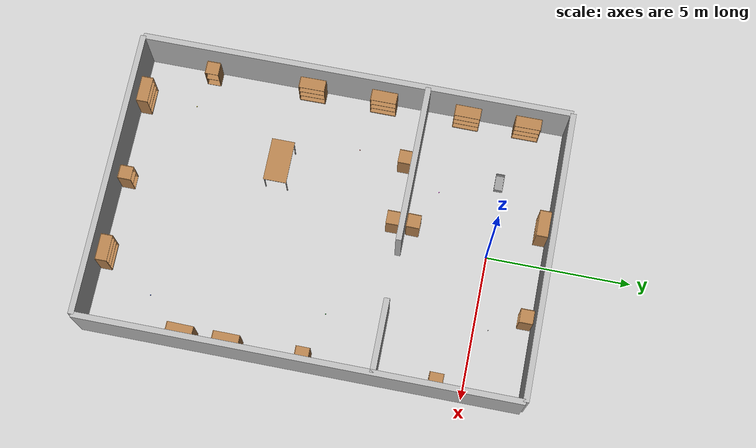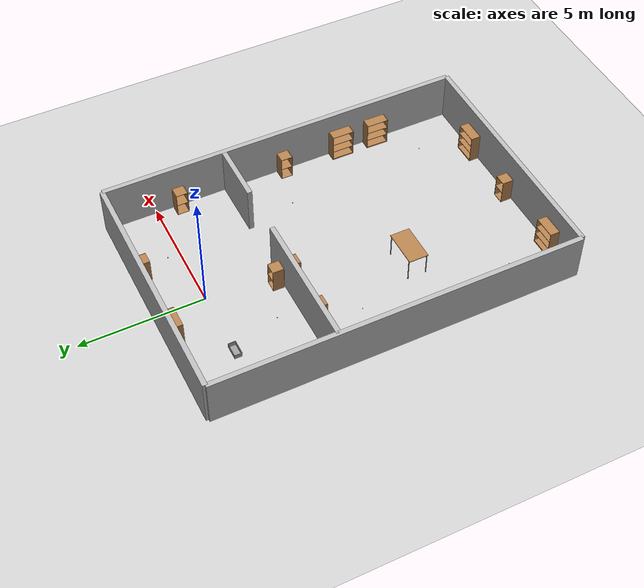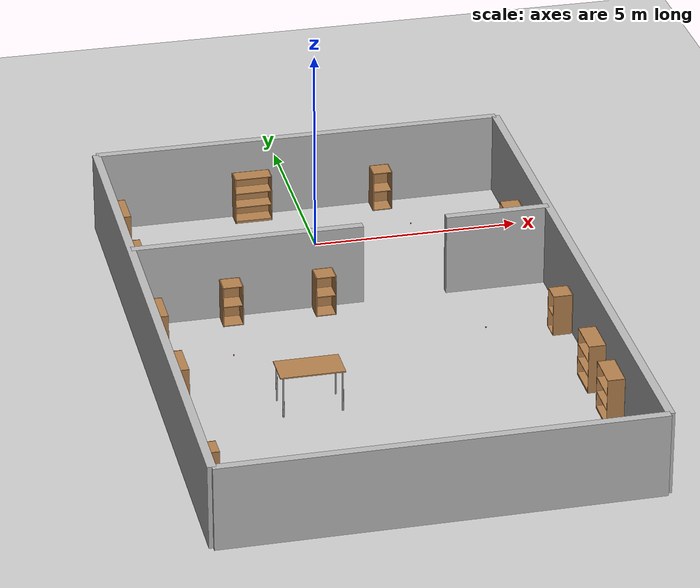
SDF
<sdf version="1.7">
 <world name="default">
  <physics type="ode">
   <ode>
    <solver>
     <type>quick</type>
     <iters>20</iters>
     <sor>1</sor>
     <use_dynamic_moi_rescaling>0</use_dynamic_moi_rescaling>
    </solver>
    <constraints>
     <cfm>0</cfm>
     <erp>0.2</erp>
     <contact_max_correcting_vel>100</contact_max_correcting_vel>
     <contact_surface_layer>0</contact_surface_layer>
    </constraints>
   </ode>
   <real_time_update_rate>1000</real_time_update_rate>
   <max_step_size>0.001</max_step_size>
   <real_time_factor>1</real_time_factor>
   <max_contacts>20</max_contacts>
  </physics>
  <light name="sun" type="directional">
   <pose>0 0 10 0 -0 0</pose>
   <diffuse>0.8 0.8 0.8 1</diffuse>
   <specular>0.2 0.2 0.2 1</specular>
   <attenuation>
    <range>1000</range>
    <constant>0.9</constant>
    <linear>0.01</linear>
    <quadratic>0.001</quadratic>
   </attenuation>
   <direction>0.5 0.1 -0.9</direction>
   <spot><inner_angle>0</inner_angle><outer_angle>0</outer_angle><falloff>0</falloff></spot>
  </light>
  <model name="ground_plane">
   <static>1</static>
   <link name="link">
    <collision name="collision">
     <geometry><plane><normal>0 0 1</normal><size>100 100</size></plane></geometry>
     <surface><friction><ode><mu>100</mu><mu2>50</mu2></ode></friction></surface>
    </collision>
    <visual name="visual">
     <cast_shadows>0</cast_shadows>
     <geometry><plane><normal>0 0 1</normal><size>100 100</size></plane></geometry>
     <material>
      <script><uri>file://media/materials/scripts/gazebo.material</uri><name>Gazebo/Grey</name></script>
     </material>
    </visual>
    <velocity_decay><linear>0</linear><angular>0</angular></velocity_decay>
   </link>
  </model>
  <model name="wall_1_model">
   <pose>0 -13 1 0 -0 0</pose>
   <static>1</static>
   <link name="wall_1_body">
    <inertial>
     <mass>1</mass>
     <inertia><ixx>1</ixx><ixy>0</ixy><ixz>0</ixz><iyy>1</iyy><iyz>0</iyz><izz>1</izz></inertia>
    </inertial>
    <collision name="collision"><geometry><box><size>10 0.2 2</size></box></geometry></collision>
    <visual name="visual"><geometry><box><size>10 0.2 2</size></box></geometry></visual>
    <velocity_decay><linear>0</linear><angular>0</angular></velocity_decay>
   </link>
  </model>
  <model name="wall_2_model">
   <pose>0 2 1 0 -0 0</pose>
   <static>1</static>
   <link name="wall_2_body">
    <inertial>
     <mass>1</mass>
     <inertia><ixx>1</ixx><ixy>0</ixy><ixz>0</ixz><iyy>1</iyy><iyz>0</iyz><izz>1</izz></inertia>
    </inertial>
    <collision name="collision"><geometry><box><size>10 0.2 2</size></box></geometry></collision>
    <visual name="visual"><geometry><box><size>10 0.2 2</size></box></geometry></visual>
    <velocity_decay><linear>0</linear><angular>0</angular></velocity_decay>
   </link>
  </model>
  <model name="wall_3_model">
   <pose>-5 -5.5 1 0 -0 0</pose>
   <static>1</static>
   <link name="wall_3_body">
    <inertial>
     <mass>1</mass>
     <inertia><ixx>1</ixx><ixy>0</ixy><ixz>0</ixz><iyy>1</iyy><iyz>0</iyz><izz>1</izz></inertia>
    </inertial>
    <collision name="collision"><geometry><box><size>0.2 15 2</size></box></geometry></collision>
    <visual name="visual"><geometry><box><size>0.2 15 2</size></box></geometry></visual>
    <velocity_decay><linear>0</linear><angular>0</angular></velocity_decay>
   </link>
  </model>
  <model name="wall_4_model">
   <pose>5 -5.5 1 0 -0 0</pose>
   <static>1</static>
   <link name="wall_4_body">
    <inertial>
     <mass>1</mass>
     <inertia><ixx>1</ixx><ixy>0</ixy><ixz>0</ixz><iyy>1</iyy><iyz>0</iyz><izz>1</izz></inertia>
    </inertial>
    <collision name="collision"><geometry><box><size>0.2 15 2</size></box></geometry></collision>
    <visual name="visual"><geometry><box><size>0.2 15 2</size></box></geometry></visual>
    <velocity_decay><linear>0</linear><angular>0</angular></velocity_decay>
   </link>
  </model>
  <model name="wall_5_model">
   <pose>-2.25 -3 1 0 -0 0</pose>
   <static>1</static>
   <link name="wall_5_body">
    <inertial>
     <mass>1</mass>
     <inertia><ixx>1</ixx><ixy>0</ixy><ixz>0</ixz><iyy>1</iyy><iyz>0</iyz><izz>1</izz></inertia>
    </inertial>
    <collision name="collision"><geometry><box><size>5.5 0.2 2</size></box></geometry></collision>
    <visual name="visual"><geometry><box><size>5.5 0.2 2</size></box></geometry></visual>
    <velocity_decay><linear>0</linear><angular>0</angular></velocity_decay>
   </link>
  </model>
  <model name="wall_6_model">
   <pose>3.75 -3 1 0 -0 0</pose>
   <static>1</static>
   <link name="wall_6_body">
    <inertial>
     <mass>1</mass>
     <inertia><ixx>1</ixx><ixy>0</ixy><ixz>0</ixz><iyy>1</iyy><iyz>0</iyz><izz>1</izz></inertia>
    </inertial>
    <collision name="collision"><geometry><box><size>2.5 0.2 2</size></box></geometry></collision>
    <visual name="visual"><geometry><box><size>2.5 0.2 2</size></box></geometry></visual>
    <velocity_decay><linear>0</linear><angular>0</angular></velocity_decay>
   </link>
  </model>
  <scene><ambient>0.2 0.2 0.2 1</ambient><background>0.7 0.7 0.7 1</background><shadows>1</shadows></scene>
  <model name="cabinet">
   <static>0</static>
   <link name="cabinet_bottom_plate">
    <inertial>
     <pose>0 0 -1 0 -0 0</pose>
     <inertia><ixx>2.05</ixx><ixy>0</ixy><ixz>0</ixz><iyy>2.05</iyy><iyz>0</iyz><izz>2.05</izz></inertia>
     <mass>25</mass>
    </inertial>
    <collision name="cabinet_bottom_plate_geom">
     <pose>0 0 0.01 0 -0 0</pose>
     <geometry><box><size>0.45 0.45 0.02</size></box></geometry>
    </collision>
    <visual name="cabinet_bottom_plate_geom_visual">
     <pose>0 0 0.01 0 -0 0</pose>
     <geometry><box><size>0.45 0.45 0.02</size></box></geometry>
     <material>
      <script><uri>file://media/materials/scripts/gazebo.material</uri><name>Gazebo/Wood</name></script>
     </material>
    </visual>
    <collision name="cabinet_bottom_plate_geom_cabinet_back_plate">
     <pose>0.235 0 0.51 0 -0 0</pose>
     <geometry><box><size>0.02 0.45 1.02</size></box></geometry>
    </collision>
    <visual name="cabinet_bottom_plate_geom_cabinet_back_plate_visual">
     <pose>0.235 0 0.51 0 -0 0</pose>
     <geometry><box><size>0.02 0.45 1.02</size></box></geometry>
     <material>
      <script><uri>file://media/materials/scripts/gazebo.material</uri><name>Gazebo/Wood</name></script>
     </material>
    </visual>
    <collision name="cabinet_bottom_plate_geom_cabinet_left_plate">
     <pose>0 0.235 0.51 0 -0 0</pose>
     <geometry><box><size>0.45 0.02 1.02</size></box></geometry>
    </collision>
    <visual name="cabinet_bottom_plate_geom_cabinet_left_plate_visual">
     <pose>0 0.235 0.51 0 -0 0</pose>
     <geometry><box><size>0.45 0.02 1.02</size></box></geometry>
     <material>
      <script><uri>file://media/materials/scripts/gazebo.material</uri><name>Gazebo/Wood</name></script>
     </material>
    </visual>
    <collision name="cabinet_bottom_plate_geom_cabinet_middle_plate">
     <pose>0 0 0.51 0 -0 0</pose>
     <geometry><box><size>0.45 0.45 0.02</size></box></geometry>
    </collision>
    <visual name="cabinet_bottom_plate_geom_cabinet_middle_plate_visual">
     <pose>0 0 0.51 0 -0 0</pose>
     <geometry><box><size>0.45 0.45 0.02</size></box></geometry>
     <material>
      <script><uri>file://media/materials/scripts/gazebo.material</uri><name>Gazebo/Wood</name></script>
     </material>
    </visual>
    <collision name="cabinet_bottom_plate_geom_cabinet_right_plate">
     <pose>0 -0.235 0.51 0 -0 0</pose>
     <geometry><box><size>0.45 0.02 1.02</size></box></geometry>
    </collision>
    <visual name="cabinet_bottom_plate_geom_cabinet_right_plate_visual">
     <pose>0 -0.235 0.51 0 -0 0</pose>
     <geometry><box><size>0.45 0.02 1.02</size></box></geometry>
     <material>
      <script><uri>file://media/materials/scripts/gazebo.material</uri><name>Gazebo/Wood</name></script>
     </material>
    </visual>
    <collision name="cabinet_bottom_plate_geom_cabinet_top_plate">
     <pose>0 0 1.01 0 -0 0</pose>
     <geometry><box><size>0.45 0.45 0.02</size></box></geometry>
    </collision>
    <visual name="cabinet_bottom_plate_geom_cabinet_top_plate_visual">
     <pose>0 0 1.01 0 -0 0</pose>
     <geometry><box><size>0.45 0.45 0.02</size></box></geometry>
     <material>
      <script><uri>file://media/materials/scripts/gazebo.material</uri><name>Gazebo/Wood</name></script>
     </material>
    </visual>
    <velocity_decay><linear>0</linear><angular>0</angular></velocity_decay>
   </link>
   <pose>2.00217 1.64704 -1e-06 -2e-06 1e-06 1.57264</pose>
  </model>
  <model name="cabinet_0">
   <static>0</static>
   <link name="cabinet_bottom_plate">
    <inertial>
     <pose>0 0 -1 0 -0 0</pose>
     <inertia><ixx>2.05</ixx><ixy>0</ixy><ixz>0</ixz><iyy>2.05</iyy><iyz>0</iyz><izz>2.05</izz></inertia>
     <mass>25</mass>
    </inertial>
    <collision name="cabinet_bottom_plate_geom">
     <pose>0 0 0.01 0 -0 0</pose>
     <geometry><box><size>0.45 0.45 0.02</size></box></geometry>
    </collision>
    <visual name="cabinet_bottom_plate_geom_visual">
     <pose>0 0 0.01 0 -0 0</pose>
     <geometry><box><size>0.45 0.45 0.02</size></box></geometry>
     <material>
      <script><uri>file://media/materials/scripts/gazebo.material</uri><name>Gazebo/Wood</name></script>
     </material>
    </visual>
    <collision name="cabinet_bottom_plate_geom_cabinet_back_plate">
     <pose>0.235 0 0.51 0 -0 0</pose>
     <geometry><box><size>0.02 0.45 1.02</size></box></geometry>
    </collision>
    <visual name="cabinet_bottom_plate_geom_cabinet_back_plate_visual">
     <pose>0.235 0 0.51 0 -0 0</pose>
     <geometry><box><size>0.02 0.45 1.02</size></box></geometry>
     <material>
      <script><uri>file://media/materials/scripts/gazebo.material</uri><name>Gazebo/Wood</name></script>
     </material>
    </visual>
    <collision name="cabinet_bottom_plate_geom_cabinet_left_plate">
     <pose>0 0.235 0.51 0 -0 0</pose>
     <geometry><box><size>0.45 0.02 1.02</size></box></geometry>
    </collision>
    <visual name="cabinet_bottom_plate_geom_cabinet_left_plate_visual">
     <pose>0 0.235 0.51 0 -0 0</pose>
     <geometry><box><size>0.45 0.02 1.02</size></box></geometry>
     <material>
      <script><uri>file://media/materials/scripts/gazebo.material</uri><name>Gazebo/Wood</name></script>
     </material>
    </visual>
    <collision name="cabinet_bottom_plate_geom_cabinet_middle_plate">
     <pose>0 0 0.51 0 -0 0</pose>
     <geometry><box><size>0.45 0.45 0.02</size></box></geometry>
    </collision>
    <visual name="cabinet_bottom_plate_geom_cabinet_middle_plate_visual">
     <pose>0 0 0.51 0 -0 0</pose>
     <geometry><box><size>0.45 0.45 0.02</size></box></geometry>
     <material>
      <script><uri>file://media/materials/scripts/gazebo.material</uri><name>Gazebo/Wood</name></script>
     </material>
    </visual>
    <collision name="cabinet_bottom_plate_geom_cabinet_right_plate">
     <pose>0 -0.235 0.51 0 -0 0</pose>
     <geometry><box><size>0.45 0.02 1.02</size></box></geometry>
    </collision>
    <visual name="cabinet_bottom_plate_geom_cabinet_right_plate_visual">
     <pose>0 -0.235 0.51 0 -0 0</pose>
     <geometry><box><size>0.45 0.02 1.02</size></box></geometry>
     <material>
      <script><uri>file://media/materials/scripts/gazebo.material</uri><name>Gazebo/Wood</name></script>
     </material>
    </visual>
    <collision name="cabinet_bottom_plate_geom_cabinet_top_plate">
     <pose>0 0 1.01 0 -0 0</pose>
     <geometry><box><size>0.45 0.45 0.02</size></box></geometry>
    </collision>
    <visual name="cabinet_bottom_plate_geom_cabinet_top_plate_visual">
     <pose>0 0 1.01 0 -0 0</pose>
     <geometry><box><size>0.45 0.45 0.02</size></box></geometry>
     <material>
      <script><uri>file://media/materials/scripts/gazebo.material</uri><name>Gazebo/Wood</name></script>
     </material>
    </visual>
    <velocity_decay><linear>0</linear><angular>0</angular></velocity_decay>
   </link>
   <pose>4.65193 -5.43983 -1e-06 -1e-06 1e-06 0.000854</pose>
  </model>
  <model name="bookshelf">
   <static>0</static>
   <link name="link">
    <inertial>
     <mass>1</mass>
     <inertia><ixx>1</ixx><ixy>0</ixy><ixz>0</ixz><iyy>1</iyy><iyz>0</iyz><izz>1</izz></inertia>
    </inertial>
    <collision name="back">
     <pose>0 0.005 0.6 0 -0 0</pose>
     <geometry><box><size>0.9 0.01 1.2</size></box></geometry>
    </collision>
    <visual name="visual1">
     <pose>0 0.005 0.6 0 -0 0</pose>
     <geometry><box><size>0.9 0.01 1.2</size></box></geometry>
     <material>
      <script><uri>file://media/materials/scripts/gazebo.material</uri><name>Gazebo/Wood</name></script>
     </material>
    </visual>
    <collision name="left_side">
     <pose>0.45 -0.195 0.6 0 -0 0</pose>
     <geometry><box><size>0.02 0.4 1.2</size></box></geometry>
    </collision>
    <visual name="visual2">
     <pose>0.45 -0.195 0.6 0 -0 0</pose>
     <geometry><box><size>0.02 0.4 1.2</size></box></geometry>
     <material>
      <script><uri>file://media/materials/scripts/gazebo.material</uri><name>Gazebo/Wood</name></script>
     </material>
    </visual>
    <collision name="right_side">
     <pose>-0.45 -0.195 0.6 0 -0 0</pose>
     <geometry><box><size>0.02 0.4 1.2</size></box></geometry>
    </collision>
    <visual name="visual3">
     <pose>-0.45 -0.195 0.6 0 -0 0</pose>
     <geometry><box><size>0.02 0.4 1.2</size></box></geometry>
     <material>
      <script><uri>file://media/materials/scripts/gazebo.material</uri><name>Gazebo/Wood</name></script>
     </material>
    </visual>
    <collision name="bottom">
     <pose>0 -0.195 0.03 0 -0 0</pose>
     <geometry><box><size>0.88 0.4 0.06</size></box></geometry>
    </collision>
    <visual name="visual4">
     <pose>0 -0.195 0.03 0 -0 0</pose>
     <geometry><box><size>0.88 0.4 0.06</size></box></geometry>
     <material>
      <script><uri>file://media/materials/scripts/gazebo.material</uri><name>Gazebo/Wood</name></script>
     </material>
    </visual>
    <collision name="top">
     <pose>0 -0.195 1.19 0 -0 0</pose>
     <geometry><box><size>0.88 0.4 0.02</size></box></geometry>
    </collision>
    <visual name="visual5">
     <pose>0 -0.195 1.19 0 -0 0</pose>
     <geometry><box><size>0.88 0.4 0.02</size></box></geometry>
     <material>
      <script><uri>file://media/materials/scripts/gazebo.material</uri><name>Gazebo/Wood</name></script>
     </material>
    </visual>
    <collision name="low_shelf">
     <pose>0 -0.195 0.43 0 -0 0</pose>
     <geometry><box><size>0.88 0.4 0.02</size></box></geometry>
    </collision>
    <visual name="visual6">
     <pose>0 -0.195 0.43 0 -0 0</pose>
     <geometry><box><size>0.88 0.4 0.02</size></box></geometry>
     <material>
      <script><uri>file://media/materials/scripts/gazebo.material</uri><name>Gazebo/Wood</name></script>
     </material>
    </visual>
    <collision name="high_shelf">
     <pose>0 -0.195 0.8 0 -0 0</pose>
     <geometry><box><size>0.88 0.4 0.02</size></box></geometry>
    </collision>
    <visual name="visual7">
     <pose>0 -0.195 0.8 0 -0 0</pose>
     <geometry><box><size>0.88 0.4 0.02</size></box></geometry>
     <material>
      <script><uri>file://media/materials/scripts/gazebo.material</uri><name>Gazebo/Wood</name></script>
     </material>
    </visual>
    <velocity_decay><linear>0</linear><angular>0</angular></velocity_decay>
   </link>
   <pose>4.88139 -9.56645 1e-06 -0 1e-06 -1.5884</pose>
  </model>
  <model name="bookshelf_0">
   <static>0</static>
   <link name="link">
    <inertial>
     <mass>1</mass>
     <inertia><ixx>1</ixx><ixy>0</ixy><ixz>0</ixz><iyy>1</iyy><iyz>0</iyz><izz>1</izz></inertia>
    </inertial>
    <collision name="back">
     <pose>0 0.005 0.6 0 -0 0</pose>
     <geometry><box><size>0.9 0.01 1.2</size></box></geometry>
    </collision>
    <visual name="visual1">
     <pose>0 0.005 0.6 0 -0 0</pose>
     <geometry><box><size>0.9 0.01 1.2</size></box></geometry>
     <material>
      <script><uri>file://media/materials/scripts/gazebo.material</uri><name>Gazebo/Wood</name></script>
     </material>
    </visual>
    <collision name="left_side">
     <pose>0.45 -0.195 0.6 0 -0 0</pose>
     <geometry><box><size>0.02 0.4 1.2</size></box></geometry>
    </collision>
    <visual name="visual2">
     <pose>0.45 -0.195 0.6 0 -0 0</pose>
     <geometry><box><size>0.02 0.4 1.2</size></box></geometry>
     <material>
      <script><uri>file://media/materials/scripts/gazebo.material</uri><name>Gazebo/Wood</name></script>
     </material>
    </visual>
    <collision name="right_side">
     <pose>-0.45 -0.195 0.6 0 -0 0</pose>
     <geometry><box><size>0.02 0.4 1.2</size></box></geometry>
    </collision>
    <visual name="visual3">
     <pose>-0.45 -0.195 0.6 0 -0 0</pose>
     <geometry><box><size>0.02 0.4 1.2</size></box></geometry>
     <material>
      <script><uri>file://media/materials/scripts/gazebo.material</uri><name>Gazebo/Wood</name></script>
     </material>
    </visual>
    <collision name="bottom">
     <pose>0 -0.195 0.03 0 -0 0</pose>
     <geometry><box><size>0.88 0.4 0.06</size></box></geometry>
    </collision>
    <visual name="visual4">
     <pose>0 -0.195 0.03 0 -0 0</pose>
     <geometry><box><size>0.88 0.4 0.06</size></box></geometry>
     <material>
      <script><uri>file://media/materials/scripts/gazebo.material</uri><name>Gazebo/Wood</name></script>
     </material>
    </visual>
    <collision name="top">
     <pose>0 -0.195 1.19 0 -0 0</pose>
     <geometry><box><size>0.88 0.4 0.02</size></box></geometry>
    </collision>
    <visual name="visual5">
     <pose>0 -0.195 1.19 0 -0 0</pose>
     <geometry><box><size>0.88 0.4 0.02</size></box></geometry>
     <material>
      <script><uri>file://media/materials/scripts/gazebo.material</uri><name>Gazebo/Wood</name></script>
     </material>
    </visual>
    <collision name="low_shelf">
     <pose>0 -0.195 0.43 0 -0 0</pose>
     <geometry><box><size>0.88 0.4 0.02</size></box></geometry>
    </collision>
    <visual name="visual6">
     <pose>0 -0.195 0.43 0 -0 0</pose>
     <geometry><box><size>0.88 0.4 0.02</size></box></geometry>
     <material>
      <script><uri>file://media/materials/scripts/gazebo.material</uri><name>Gazebo/Wood</name></script>
     </material>
    </visual>
    <collision name="high_shelf">
     <pose>0 -0.195 0.8 0 -0 0</pose>
     <geometry><box><size>0.88 0.4 0.02</size></box></geometry>
    </collision>
    <visual name="visual7">
     <pose>0 -0.195 0.8 0 -0 0</pose>
     <geometry><box><size>0.88 0.4 0.02</size></box></geometry>
     <material>
      <script><uri>file://media/materials/scripts/gazebo.material</uri><name>Gazebo/Wood</name></script>
     </material>
    </visual>
    <velocity_decay><linear>0</linear><angular>0</angular></velocity_decay>
   </link>
   <pose>-4.88413 -1.51974 1e-06 0 1e-06 1.56443</pose>
  </model>
  <model name="bookshelf_1">
   <static>0</static>
   <link name="link">
    <inertial>
     <mass>1</mass>
     <inertia><ixx>1</ixx><ixy>0</ixy><ixz>0</ixz><iyy>1</iyy><iyz>0</iyz><izz>1</izz></inertia>
    </inertial>
    <collision name="back">
     <pose>0 0.005 0.6 0 -0 0</pose>
     <geometry><box><size>0.9 0.01 1.2</size></box></geometry>
    </collision>
    <visual name="visual1">
     <pose>0 0.005 0.6 0 -0 0</pose>
     <geometry><box><size>0.9 0.01 1.2</size></box></geometry>
     <material>
      <script><uri>file://media/materials/scripts/gazebo.material</uri><name>Gazebo/Wood</name></script>
     </material>
    </visual>
    <collision name="left_side">
     <pose>0.45 -0.195 0.6 0 -0 0</pose>
     <geometry><box><size>0.02 0.4 1.2</size></box></geometry>
    </collision>
    <visual name="visual2">
     <pose>0.45 -0.195 0.6 0 -0 0</pose>
     <geometry><box><size>0.02 0.4 1.2</size></box></geometry>
     <material>
      <script><uri>file://media/materials/scripts/gazebo.material</uri><name>Gazebo/Wood</name></script>
     </material>
    </visual>
    <collision name="right_side">
     <pose>-0.45 -0.195 0.6 0 -0 0</pose>
     <geometry><box><size>0.02 0.4 1.2</size></box></geometry>
    </collision>
    <visual name="visual3">
     <pose>-0.45 -0.195 0.6 0 -0 0</pose>
     <geometry><box><size>0.02 0.4 1.2</size></box></geometry>
     <material>
      <script><uri>file://media/materials/scripts/gazebo.material</uri><name>Gazebo/Wood</name></script>
     </material>
    </visual>
    <collision name="bottom">
     <pose>0 -0.195 0.03 0 -0 0</pose>
     <geometry><box><size>0.88 0.4 0.06</size></box></geometry>
    </collision>
    <visual name="visual4">
     <pose>0 -0.195 0.03 0 -0 0</pose>
     <geometry><box><size>0.88 0.4 0.06</size></box></geometry>
     <material>
      <script><uri>file://media/materials/scripts/gazebo.material</uri><name>Gazebo/Wood</name></script>
     </material>
    </visual>
    <collision name="top">
     <pose>0 -0.195 1.19 0 -0 0</pose>
     <geometry><box><size>0.88 0.4 0.02</size></box></geometry>
    </collision>
    <visual name="visual5">
     <pose>0 -0.195 1.19 0 -0 0</pose>
     <geometry><box><size>0.88 0.4 0.02</size></box></geometry>
     <material>
      <script><uri>file://media/materials/scripts/gazebo.material</uri><name>Gazebo/Wood</name></script>
     </material>
    </visual>
    <collision name="low_shelf">
     <pose>0 -0.195 0.43 0 -0 0</pose>
     <geometry><box><size>0.88 0.4 0.02</size></box></geometry>
    </collision>
    <visual name="visual6">
     <pose>0 -0.195 0.43 0 -0 0</pose>
     <geometry><box><size>0.88 0.4 0.02</size></box></geometry>
     <material>
      <script><uri>file://media/materials/scripts/gazebo.material</uri><name>Gazebo/Wood</name></script>
     </material>
    </visual>
    <collision name="high_shelf">
     <pose>0 -0.195 0.8 0 -0 0</pose>
     <geometry><box><size>0.88 0.4 0.02</size></box></geometry>
    </collision>
    <visual name="visual7">
     <pose>0 -0.195 0.8 0 -0 0</pose>
     <geometry><box><size>0.88 0.4 0.02</size></box></geometry>
     <material>
      <script><uri>file://media/materials/scripts/gazebo.material</uri><name>Gazebo/Wood</name></script>
     </material>
    </visual>
    <velocity_decay><linear>0</linear><angular>0</angular></velocity_decay>
   </link>
   <pose>-4.88539 0.594654 -1e-06 0 3e-06 1.57477</pose>
  </model>
  <model name="cabinet_1">
   <static>0</static>
   <link name="cabinet_bottom_plate">
    <inertial>
     <pose>0 0 -1 0 -0 0</pose>
     <inertia><ixx>2.05</ixx><ixy>0</ixy><ixz>0</ixz><iyy>2.05</iyy><iyz>0</iyz><izz>2.05</izz></inertia>
     <mass>25</mass>
    </inertial>
    <collision name="cabinet_bottom_plate_geom">
     <pose>0 0 0.01 0 -0 0</pose>
     <geometry><box><size>0.45 0.45 0.02</size></box></geometry>
    </collision>
    <visual name="cabinet_bottom_plate_geom_visual">
     <pose>0 0 0.01 0 -0 0</pose>
     <geometry><box><size>0.45 0.45 0.02</size></box></geometry>
     <material>
      <script><uri>file://media/materials/scripts/gazebo.material</uri><name>Gazebo/Wood</name></script>
     </material>
    </visual>
    <collision name="cabinet_bottom_plate_geom_cabinet_back_plate">
     <pose>0.235 0 0.51 0 -0 0</pose>
     <geometry><box><size>0.02 0.45 1.02</size></box></geometry>
    </collision>
    <visual name="cabinet_bottom_plate_geom_cabinet_back_plate_visual">
     <pose>0.235 0 0.51 0 -0 0</pose>
     <geometry><box><size>0.02 0.45 1.02</size></box></geometry>
     <material>
      <script><uri>file://media/materials/scripts/gazebo.material</uri><name>Gazebo/Wood</name></script>
     </material>
    </visual>
    <collision name="cabinet_bottom_plate_geom_cabinet_left_plate">
     <pose>0 0.235 0.51 0 -0 0</pose>
     <geometry><box><size>0.45 0.02 1.02</size></box></geometry>
    </collision>
    <visual name="cabinet_bottom_plate_geom_cabinet_left_plate_visual">
     <pose>0 0.235 0.51 0 -0 0</pose>
     <geometry><box><size>0.45 0.02 1.02</size></box></geometry>
     <material>
      <script><uri>file://media/materials/scripts/gazebo.material</uri><name>Gazebo/Wood</name></script>
     </material>
    </visual>
    <collision name="cabinet_bottom_plate_geom_cabinet_middle_plate">
     <pose>0 0 0.51 0 -0 0</pose>
     <geometry><box><size>0.45 0.45 0.02</size></box></geometry>
    </collision>
    <visual name="cabinet_bottom_plate_geom_cabinet_middle_plate_visual">
     <pose>0 0 0.51 0 -0 0</pose>
     <geometry><box><size>0.45 0.45 0.02</size></box></geometry>
     <material>
      <script><uri>file://media/materials/scripts/gazebo.material</uri><name>Gazebo/Wood</name></script>
     </material>
    </visual>
    <collision name="cabinet_bottom_plate_geom_cabinet_right_plate">
     <pose>0 -0.235 0.51 0 -0 0</pose>
     <geometry><box><size>0.45 0.02 1.02</size></box></geometry>
    </collision>
    <visual name="cabinet_bottom_plate_geom_cabinet_right_plate_visual">
     <pose>0 -0.235 0.51 0 -0 0</pose>
     <geometry><box><size>0.45 0.02 1.02</size></box></geometry>
     <material>
      <script><uri>file://media/materials/scripts/gazebo.material</uri><name>Gazebo/Wood</name></script>
     </material>
    </visual>
    <collision name="cabinet_bottom_plate_geom_cabinet_top_plate">
     <pose>0 0 1.01 0 -0 0</pose>
     <geometry><box><size>0.45 0.45 0.02</size></box></geometry>
    </collision>
    <visual name="cabinet_bottom_plate_geom_cabinet_top_plate_visual">
     <pose>0 0 1.01 0 -0 0</pose>
     <geometry><box><size>0.45 0.45 0.02</size></box></geometry>
     <material>
      <script><uri>file://media/materials/scripts/gazebo.material</uri><name>Gazebo/Wood</name></script>
     </material>
    </visual>
    <velocity_decay><linear>0</linear><angular>0</angular></velocity_decay>
   </link>
   <pose>-2.72476 -3.35344 1e-06 -0 -3e-06 1.56613</pose>
  </model>
  <model name="cabinet_2">
   <static>0</static>
   <link name="cabinet_bottom_plate">
    <inertial>
     <pose>0 0 -1 0 -0 0</pose>
     <inertia><ixx>2.05</ixx><ixy>0</ixy><ixz>0</ixz><iyy>2.05</iyy><iyz>0</iyz><izz>2.05</izz></inertia>
     <mass>25</mass>
    </inertial>
    <collision name="cabinet_bottom_plate_geom">
     <pose>0 0 0.01 0 -0 0</pose>
     <geometry><box><size>0.45 0.45 0.02</size></box></geometry>
    </collision>
    <visual name="cabinet_bottom_plate_geom_visual">
     <pose>0 0 0.01 0 -0 0</pose>
     <geometry><box><size>0.45 0.45 0.02</size></box></geometry>
     <material>
      <script><uri>file://media/materials/scripts/gazebo.material</uri><name>Gazebo/Wood</name></script>
     </material>
    </visual>
    <collision name="cabinet_bottom_plate_geom_cabinet_back_plate">
     <pose>0.235 0 0.51 0 -0 0</pose>
     <geometry><box><size>0.02 0.45 1.02</size></box></geometry>
    </collision>
    <visual name="cabinet_bottom_plate_geom_cabinet_back_plate_visual">
     <pose>0.235 0 0.51 0 -0 0</pose>
     <geometry><box><size>0.02 0.45 1.02</size></box></geometry>
     <material>
      <script><uri>file://media/materials/scripts/gazebo.material</uri><name>Gazebo/Wood</name></script>
     </material>
    </visual>
    <collision name="cabinet_bottom_plate_geom_cabinet_left_plate">
     <pose>0 0.235 0.51 0 -0 0</pose>
     <geometry><box><size>0.45 0.02 1.02</size></box></geometry>
    </collision>
    <visual name="cabinet_bottom_plate_geom_cabinet_left_plate_visual">
     <pose>0 0.235 0.51 0 -0 0</pose>
     <geometry><box><size>0.45 0.02 1.02</size></box></geometry>
     <material>
      <script><uri>file://media/materials/scripts/gazebo.material</uri><name>Gazebo/Wood</name></script>
     </material>
    </visual>
    <collision name="cabinet_bottom_plate_geom_cabinet_middle_plate">
     <pose>0 0 0.51 0 -0 0</pose>
     <geometry><box><size>0.45 0.45 0.02</size></box></geometry>
    </collision>
    <visual name="cabinet_bottom_plate_geom_cabinet_middle_plate_visual">
     <pose>0 0 0.51 0 -0 0</pose>
     <geometry><box><size>0.45 0.45 0.02</size></box></geometry>
     <material>
      <script><uri>file://media/materials/scripts/gazebo.material</uri><name>Gazebo/Wood</name></script>
     </material>
    </visual>
    <collision name="cabinet_bottom_plate_geom_cabinet_right_plate">
     <pose>0 -0.235 0.51 0 -0 0</pose>
     <geometry><box><size>0.45 0.02 1.02</size></box></geometry>
    </collision>
    <visual name="cabinet_bottom_plate_geom_cabinet_right_plate_visual">
     <pose>0 -0.235 0.51 0 -0 0</pose>
     <geometry><box><size>0.45 0.02 1.02</size></box></geometry>
     <material>
      <script><uri>file://media/materials/scripts/gazebo.material</uri><name>Gazebo/Wood</name></script>
     </material>
    </visual>
    <collision name="cabinet_bottom_plate_geom_cabinet_top_plate">
     <pose>0 0 1.01 0 -0 0</pose>
     <geometry><box><size>0.45 0.45 0.02</size></box></geometry>
    </collision>
    <visual name="cabinet_bottom_plate_geom_cabinet_top_plate_visual">
     <pose>0 0 1.01 0 -0 0</pose>
     <geometry><box><size>0.45 0.45 0.02</size></box></geometry>
     <material>
      <script><uri>file://media/materials/scripts/gazebo.material</uri><name>Gazebo/Wood</name></script>
     </material>
    </visual>
    <velocity_decay><linear>0</linear><angular>0</angular></velocity_decay>
   </link>
   <pose>-0.506055 -3.35059 0 0 2e-06 1.57749</pose>
  </model>
  <model name="bookshelf_2">
   <static>0</static>
   <link name="link">
    <inertial>
     <mass>1</mass>
     <inertia><ixx>1</ixx><ixy>0</ixy><ixz>0</ixz><iyy>1</iyy><iyz>0</iyz><izz>1</izz></inertia>
    </inertial>
    <collision name="back">
     <pose>0 0.005 0.6 0 -0 0</pose>
     <geometry><box><size>0.9 0.01 1.2</size></box></geometry>
    </collision>
    <visual name="visual1">
     <pose>0 0.005 0.6 0 -0 0</pose>
     <geometry><box><size>0.9 0.01 1.2</size></box></geometry>
     <material>
      <script><uri>file://media/materials/scripts/gazebo.material</uri><name>Gazebo/Wood</name></script>
     </material>
    </visual>
    <collision name="left_side">
     <pose>0.45 -0.195 0.6 0 -0 0</pose>
     <geometry><box><size>0.02 0.4 1.2</size></box></geometry>
    </collision>
    <visual name="visual2">
     <pose>0.45 -0.195 0.6 0 -0 0</pose>
     <geometry><box><size>0.02 0.4 1.2</size></box></geometry>
     <material>
      <script><uri>file://media/materials/scripts/gazebo.material</uri><name>Gazebo/Wood</name></script>
     </material>
    </visual>
    <collision name="right_side">
     <pose>-0.45 -0.195 0.6 0 -0 0</pose>
     <geometry><box><size>0.02 0.4 1.2</size></box></geometry>
    </collision>
    <visual name="visual3">
     <pose>-0.45 -0.195 0.6 0 -0 0</pose>
     <geometry><box><size>0.02 0.4 1.2</size></box></geometry>
     <material>
      <script><uri>file://media/materials/scripts/gazebo.material</uri><name>Gazebo/Wood</name></script>
     </material>
    </visual>
    <collision name="bottom">
     <pose>0 -0.195 0.03 0 -0 0</pose>
     <geometry><box><size>0.88 0.4 0.06</size></box></geometry>
    </collision>
    <visual name="visual4">
     <pose>0 -0.195 0.03 0 -0 0</pose>
     <geometry><box><size>0.88 0.4 0.06</size></box></geometry>
     <material>
      <script><uri>file://media/materials/scripts/gazebo.material</uri><name>Gazebo/Wood</name></script>
     </material>
    </visual>
    <collision name="top">
     <pose>0 -0.195 1.19 0 -0 0</pose>
     <geometry><box><size>0.88 0.4 0.02</size></box></geometry>
    </collision>
    <visual name="visual5">
     <pose>0 -0.195 1.19 0 -0 0</pose>
     <geometry><box><size>0.88 0.4 0.02</size></box></geometry>
     <material>
      <script><uri>file://media/materials/scripts/gazebo.material</uri><name>Gazebo/Wood</name></script>
     </material>
    </visual>
    <collision name="low_shelf">
     <pose>0 -0.195 0.43 0 -0 0</pose>
     <geometry><box><size>0.88 0.4 0.02</size></box></geometry>
    </collision>
    <visual name="visual6">
     <pose>0 -0.195 0.43 0 -0 0</pose>
     <geometry><box><size>0.88 0.4 0.02</size></box></geometry>
     <material>
      <script><uri>file://media/materials/scripts/gazebo.material</uri><name>Gazebo/Wood</name></script>
     </material>
    </visual>
    <collision name="high_shelf">
     <pose>0 -0.195 0.8 0 -0 0</pose>
     <geometry><box><size>0.88 0.4 0.02</size></box></geometry>
    </collision>
    <visual name="visual7">
     <pose>0 -0.195 0.8 0 -0 0</pose>
     <geometry><box><size>0.88 0.4 0.02</size></box></geometry>
     <material>
      <script><uri>file://media/materials/scripts/gazebo.material</uri><name>Gazebo/Wood</name></script>
     </material>
    </visual>
    <velocity_decay><linear>0</linear><angular>0</angular></velocity_decay>
   </link>
   <pose>-4.86972 -7.01077 1e-06 0 1e-06 1.57822</pose>
  </model>
  <model name="table_1">
   <static>0</static>
   <link name="link">
    <collision name="surface">
     <pose>0 0 1 0 -0 0</pose>
     <geometry><box><size>1.5 0.8 0.03</size></box></geometry>
    </collision>
    <visual name="visual1">
     <pose>0 0 1 0 -0 0</pose>
     <geometry><box><size>1.5 0.8 0.03</size></box></geometry>
     <material>
      <script><uri>file://media/materials/scripts/gazebo.material</uri><name>Gazebo/Wood</name></script>
     </material>
    </visual>
    <collision name="front_left_leg_collision">
     <pose>0.68 0.38 0.5 0 -0 0</pose>
     <geometry><cylinder><radius>0.02</radius><length>1</length></cylinder></geometry>
    </collision>
    <visual name="front_left_leg">
     <pose>0.68 0.38 0.5 0 -0 0</pose>
     <geometry><cylinder><radius>0.02</radius><length>1</length></cylinder></geometry>
     <material>
      <script><uri>file://media/materials/scripts/gazebo.material</uri><name>Gazebo/Grey</name></script>
     </material>
    </visual>
    <collision name="front_right_leg_collision">
     <pose>0.68 -0.38 0.5 0 -0 0</pose>
     <geometry><cylinder><radius>0.02</radius><length>1</length></cylinder></geometry>
    </collision>
    <visual name="front_right_leg">
     <pose>0.68 -0.38 0.5 0 -0 0</pose>
     <geometry><cylinder><radius>0.02</radius><length>1</length></cylinder></geometry>
     <material>
      <script><uri>file://media/materials/scripts/gazebo.material</uri><name>Gazebo/Grey</name></script>
     </material>
    </visual>
    <collision name="back_right_leg_collision">
     <pose>-0.68 -0.38 0.5 0 -0 0</pose>
     <geometry><cylinder><radius>0.02</radius><length>1</length></cylinder></geometry>
    </collision>
    <visual name="back_right_leg">
     <pose>-0.68 -0.38 0.5 0 -0 0</pose>
     <geometry><cylinder><radius>0.02</radius><length>1</length></cylinder></geometry>
     <material>
      <script><uri>file://media/materials/scripts/gazebo.material</uri><name>Gazebo/Grey</name></script>
     </material>
    </visual>
    <collision name="back_left_leg_collision">
     <pose>-0.68 0.38 0.5 0 -0 0</pose>
     <geometry><cylinder><radius>0.02</radius><length>1</length></cylinder></geometry>
    </collision>
    <visual name="back_left_leg">
     <pose>-0.68 0.38 0.5 0 -0 0</pose>
     <geometry><cylinder><radius>0.02</radius><length>1</length></cylinder></geometry>
     <material>
      <script><uri>file://media/materials/scripts/gazebo.material</uri><name>Gazebo/Grey</name></script>
     </material>
    </visual>
    <velocity_decay><linear>0</linear><angular>0</angular></velocity_decay>
    <inertial>
     <inertia><ixx>1</ixx><ixy>0</ixy><ixz>0</ixz><iyy>1</iyy><iyz>0</iyz><izz>1</izz></inertia>
     <mass>1</mass>
    </inertial>
   </link>
   <pose>-1.76173 -7.584 -1e-06 0 2e-06 0</pose>
  </model>
  <model name="cabinet_3">
   <static>0</static>
   <link name="cabinet_bottom_plate">
    <inertial>
     <pose>0 0 -1 0 -0 0</pose>
     <inertia><ixx>2.05</ixx><ixy>0</ixy><ixz>0</ixz><iyy>2.05</iyy><iyz>0</iyz><izz>2.05</izz></inertia>
     <mass>25</mass>
    </inertial>
    <collision name="cabinet_bottom_plate_geom">
     <pose>0 0 0.01 0 -0 0</pose>
     <geometry><box><size>0.45 0.45 0.02</size></box></geometry>
    </collision>
    <visual name="cabinet_bottom_plate_geom_visual">
     <pose>0 0 0.01 0 -0 0</pose>
     <geometry><box><size>0.45 0.45 0.02</size></box></geometry>
     <material>
      <script><uri>file://media/materials/scripts/gazebo.material</uri><name>Gazebo/Wood</name></script>
     </material>
    </visual>
    <collision name="cabinet_bottom_plate_geom_cabinet_back_plate">
     <pose>0.235 0 0.51 0 -0 0</pose>
     <geometry><box><size>0.02 0.45 1.02</size></box></geometry>
    </collision>
    <visual name="cabinet_bottom_plate_geom_cabinet_back_plate_visual">
     <pose>0.235 0 0.51 0 -0 0</pose>
     <geometry><box><size>0.02 0.45 1.02</size></box></geometry>
     <material>
      <script><uri>file://media/materials/scripts/gazebo.material</uri><name>Gazebo/Wood</name></script>
     </material>
    </visual>
    <collision name="cabinet_bottom_plate_geom_cabinet_left_plate">
     <pose>0 0.235 0.51 0 -0 0</pose>
     <geometry><box><size>0.45 0.02 1.02</size></box></geometry>
    </collision>
    <visual name="cabinet_bottom_plate_geom_cabinet_left_plate_visual">
     <pose>0 0.235 0.51 0 -0 0</pose>
     <geometry><box><size>0.45 0.02 1.02</size></box></geometry>
     <material>
      <script><uri>file://media/materials/scripts/gazebo.material</uri><name>Gazebo/Wood</name></script>
     </material>
    </visual>
    <collision name="cabinet_bottom_plate_geom_cabinet_middle_plate">
     <pose>0 0 0.51 0 -0 0</pose>
     <geometry><box><size>0.45 0.45 0.02</size></box></geometry>
    </collision>
    <visual name="cabinet_bottom_plate_geom_cabinet_middle_plate_visual">
     <pose>0 0 0.51 0 -0 0</pose>
     <geometry><box><size>0.45 0.45 0.02</size></box></geometry>
     <material>
      <script><uri>file://media/materials/scripts/gazebo.material</uri><name>Gazebo/Wood</name></script>
     </material>
    </visual>
    <collision name="cabinet_bottom_plate_geom_cabinet_right_plate">
     <pose>0 -0.235 0.51 0 -0 0</pose>
     <geometry><box><size>0.45 0.02 1.02</size></box></geometry>
    </collision>
    <visual name="cabinet_bottom_plate_geom_cabinet_right_plate_visual">
     <pose>0 -0.235 0.51 0 -0 0</pose>
     <geometry><box><size>0.45 0.02 1.02</size></box></geometry>
     <material>
      <script><uri>file://media/materials/scripts/gazebo.material</uri><name>Gazebo/Wood</name></script>
     </material>
    </visual>
    <collision name="cabinet_bottom_plate_geom_cabinet_top_plate">
     <pose>0 0 1.01 0 -0 0</pose>
     <geometry><box><size>0.45 0.45 0.02</size></box></geometry>
    </collision>
    <visual name="cabinet_bottom_plate_geom_cabinet_top_plate_visual">
     <pose>0 0 1.01 0 -0 0</pose>
     <geometry><box><size>0.45 0.45 0.02</size></box></geometry>
     <material>
      <script><uri>file://media/materials/scripts/gazebo.material</uri><name>Gazebo/Wood</name></script>
     </material>
    </visual>
    <velocity_decay><linear>0</linear><angular>0</angular></velocity_decay>
   </link>
   <pose>4.65389 -0.942113 1e-06 -5e-06 -0 -0.004882</pose>
  </model>
  <model name="bookshelf_3">
   <static>0</static>
   <link name="link">
    <inertial>
     <mass>1</mass>
     <inertia><ixx>1</ixx><ixy>0</ixy><ixz>0</ixz><iyy>1</iyy><iyz>0</iyz><izz>1</izz></inertia>
    </inertial>
    <collision name="back">
     <pose>0 0.005 0.6 0 -0 0</pose>
     <geometry><box><size>0.9 0.01 1.2</size></box></geometry>
    </collision>
    <visual name="visual1">
     <pose>0 0.005 0.6 0 -0 0</pose>
     <geometry><box><size>0.9 0.01 1.2</size></box></geometry>
     <material>
      <script><uri>file://media/materials/scripts/gazebo.material</uri><name>Gazebo/Wood</name></script>
     </material>
    </visual>
    <collision name="left_side">
     <pose>0.45 -0.195 0.6 0 -0 0</pose>
     <geometry><box><size>0.02 0.4 1.2</size></box></geometry>
    </collision>
    <visual name="visual2">
     <pose>0.45 -0.195 0.6 0 -0 0</pose>
     <geometry><box><size>0.02 0.4 1.2</size></box></geometry>
     <material>
      <script><uri>file://media/materials/scripts/gazebo.material</uri><name>Gazebo/Wood</name></script>
     </material>
    </visual>
    <collision name="right_side">
     <pose>-0.45 -0.195 0.6 0 -0 0</pose>
     <geometry><box><size>0.02 0.4 1.2</size></box></geometry>
    </collision>
    <visual name="visual3">
     <pose>-0.45 -0.195 0.6 0 -0 0</pose>
     <geometry><box><size>0.02 0.4 1.2</size></box></geometry>
     <material>
      <script><uri>file://media/materials/scripts/gazebo.material</uri><name>Gazebo/Wood</name></script>
     </material>
    </visual>
    <collision name="bottom">
     <pose>0 -0.195 0.03 0 -0 0</pose>
     <geometry><box><size>0.88 0.4 0.06</size></box></geometry>
    </collision>
    <visual name="visual4">
     <pose>0 -0.195 0.03 0 -0 0</pose>
     <geometry><box><size>0.88 0.4 0.06</size></box></geometry>
     <material>
      <script><uri>file://media/materials/scripts/gazebo.material</uri><name>Gazebo/Wood</name></script>
     </material>
    </visual>
    <collision name="top">
     <pose>0 -0.195 1.19 0 -0 0</pose>
     <geometry><box><size>0.88 0.4 0.02</size></box></geometry>
    </collision>
    <visual name="visual5">
     <pose>0 -0.195 1.19 0 -0 0</pose>
     <geometry><box><size>0.88 0.4 0.02</size></box></geometry>
     <material>
      <script><uri>file://media/materials/scripts/gazebo.material</uri><name>Gazebo/Wood</name></script>
     </material>
    </visual>
    <collision name="low_shelf">
     <pose>0 -0.195 0.43 0 -0 0</pose>
     <geometry><box><size>0.88 0.4 0.02</size></box></geometry>
    </collision>
    <visual name="visual6">
     <pose>0 -0.195 0.43 0 -0 0</pose>
     <geometry><box><size>0.88 0.4 0.02</size></box></geometry>
     <material>
      <script><uri>file://media/materials/scripts/gazebo.material</uri><name>Gazebo/Wood</name></script>
     </material>
    </visual>
    <collision name="high_shelf">
     <pose>0 -0.195 0.8 0 -0 0</pose>
     <geometry><box><size>0.88 0.4 0.02</size></box></geometry>
    </collision>
    <visual name="visual7">
     <pose>0 -0.195 0.8 0 -0 0</pose>
     <geometry><box><size>0.88 0.4 0.02</size></box></geometry>
     <material>
      <script><uri>file://media/materials/scripts/gazebo.material</uri><name>Gazebo/Wood</name></script>
     </material>
    </visual>
    <velocity_decay><linear>0</linear><angular>0</angular></velocity_decay>
   </link>
   <pose>2.43147 -12.8834 -1e-06 -0 -3e-06 -3.13362</pose>
  </model>
  <model name="bookshelf_4">
   <static>0</static>
   <link name="link">
    <inertial>
     <mass>1</mass>
     <inertia><ixx>1</ixx><ixy>0</ixy><ixz>0</ixz><iyy>1</iyy><iyz>0</iyz><izz>1</izz></inertia>
    </inertial>
    <collision name="back">
     <pose>0 0.005 0.6 0 -0 0</pose>
     <geometry><box><size>0.9 0.01 1.2</size></box></geometry>
    </collision>
    <visual name="visual1">
     <pose>0 0.005 0.6 0 -0 0</pose>
     <geometry><box><size>0.9 0.01 1.2</size></box></geometry>
     <material>
      <script><uri>file://media/materials/scripts/gazebo.material</uri><name>Gazebo/Wood</name></script>
     </material>
    </visual>
    <collision name="left_side">
     <pose>0.45 -0.195 0.6 0 -0 0</pose>
     <geometry><box><size>0.02 0.4 1.2</size></box></geometry>
    </collision>
    <visual name="visual2">
     <pose>0.45 -0.195 0.6 0 -0 0</pose>
     <geometry><box><size>0.02 0.4 1.2</size></box></geometry>
     <material>
      <script><uri>file://media/materials/scripts/gazebo.material</uri><name>Gazebo/Wood</name></script>
     </material>
    </visual>
    <collision name="right_side">
     <pose>-0.45 -0.195 0.6 0 -0 0</pose>
     <geometry><box><size>0.02 0.4 1.2</size></box></geometry>
    </collision>
    <visual name="visual3">
     <pose>-0.45 -0.195 0.6 0 -0 0</pose>
     <geometry><box><size>0.02 0.4 1.2</size></box></geometry>
     <material>
      <script><uri>file://media/materials/scripts/gazebo.material</uri><name>Gazebo/Wood</name></script>
     </material>
    </visual>
    <collision name="bottom">
     <pose>0 -0.195 0.03 0 -0 0</pose>
     <geometry><box><size>0.88 0.4 0.06</size></box></geometry>
    </collision>
    <visual name="visual4">
     <pose>0 -0.195 0.03 0 -0 0</pose>
     <geometry><box><size>0.88 0.4 0.06</size></box></geometry>
     <material>
      <script><uri>file://media/materials/scripts/gazebo.material</uri><name>Gazebo/Wood</name></script>
     </material>
    </visual>
    <collision name="top">
     <pose>0 -0.195 1.19 0 -0 0</pose>
     <geometry><box><size>0.88 0.4 0.02</size></box></geometry>
    </collision>
    <visual name="visual5">
     <pose>0 -0.195 1.19 0 -0 0</pose>
     <geometry><box><size>0.88 0.4 0.02</size></box></geometry>
     <material>
      <script><uri>file://media/materials/scripts/gazebo.material</uri><name>Gazebo/Wood</name></script>
     </material>
    </visual>
    <collision name="low_shelf">
     <pose>0 -0.195 0.43 0 -0 0</pose>
     <geometry><box><size>0.88 0.4 0.02</size></box></geometry>
    </collision>
    <visual name="visual6">
     <pose>0 -0.195 0.43 0 -0 0</pose>
     <geometry><box><size>0.88 0.4 0.02</size></box></geometry>
     <material>
      <script><uri>file://media/materials/scripts/gazebo.material</uri><name>Gazebo/Wood</name></script>
     </material>
    </visual>
    <collision name="high_shelf">
     <pose>0 -0.195 0.8 0 -0 0</pose>
     <geometry><box><size>0.88 0.4 0.02</size></box></geometry>
    </collision>
    <visual name="visual7">
     <pose>0 -0.195 0.8 0 -0 0</pose>
     <geometry><box><size>0.88 0.4 0.02</size></box></geometry>
     <material>
      <script><uri>file://media/materials/scripts/gazebo.material</uri><name>Gazebo/Wood</name></script>
     </material>
    </visual>
    <velocity_decay><linear>0</linear><angular>0</angular></velocity_decay>
   </link>
   <pose>4.88559 -7.99576 -1e-06 0 3e-06 -1.57572</pose>
  </model>
  <model name="bookshelf_5">
   <static>0</static>
   <link name="link">
    <inertial>
     <mass>1</mass>
     <inertia><ixx>1</ixx><ixy>0</ixy><ixz>0</ixz><iyy>1</iyy><iyz>0</iyz><izz>1</izz></inertia>
    </inertial>
    <collision name="back">
     <pose>0 0.005 0.6 0 -0 0</pose>
     <geometry><box><size>0.9 0.01 1.2</size></box></geometry>
    </collision>
    <visual name="visual1">
     <pose>0 0.005 0.6 0 -0 0</pose>
     <geometry><box><size>0.9 0.01 1.2</size></box></geometry>
     <material>
      <script><uri>file://media/materials/scripts/gazebo.material</uri><name>Gazebo/Wood</name></script>
     </material>
    </visual>
    <collision name="left_side">
     <pose>0.45 -0.195 0.6 0 -0 0</pose>
     <geometry><box><size>0.02 0.4 1.2</size></box></geometry>
    </collision>
    <visual name="visual2">
     <pose>0.45 -0.195 0.6 0 -0 0</pose>
     <geometry><box><size>0.02 0.4 1.2</size></box></geometry>
     <material>
      <script><uri>file://media/materials/scripts/gazebo.material</uri><name>Gazebo/Wood</name></script>
     </material>
    </visual>
    <collision name="right_side">
     <pose>-0.45 -0.195 0.6 0 -0 0</pose>
     <geometry><box><size>0.02 0.4 1.2</size></box></geometry>
    </collision>
    <visual name="visual3">
     <pose>-0.45 -0.195 0.6 0 -0 0</pose>
     <geometry><box><size>0.02 0.4 1.2</size></box></geometry>
     <material>
      <script><uri>file://media/materials/scripts/gazebo.material</uri><name>Gazebo/Wood</name></script>
     </material>
    </visual>
    <collision name="bottom">
     <pose>0 -0.195 0.03 0 -0 0</pose>
     <geometry><box><size>0.88 0.4 0.06</size></box></geometry>
    </collision>
    <visual name="visual4">
     <pose>0 -0.195 0.03 0 -0 0</pose>
     <geometry><box><size>0.88 0.4 0.06</size></box></geometry>
     <material>
      <script><uri>file://media/materials/scripts/gazebo.material</uri><name>Gazebo/Wood</name></script>
     </material>
    </visual>
    <collision name="top">
     <pose>0 -0.195 1.19 0 -0 0</pose>
     <geometry><box><size>0.88 0.4 0.02</size></box></geometry>
    </collision>
    <visual name="visual5">
     <pose>0 -0.195 1.19 0 -0 0</pose>
     <geometry><box><size>0.88 0.4 0.02</size></box></geometry>
     <material>
      <script><uri>file://media/materials/scripts/gazebo.material</uri><name>Gazebo/Wood</name></script>
     </material>
    </visual>
    <collision name="low_shelf">
     <pose>0 -0.195 0.43 0 -0 0</pose>
     <geometry><box><size>0.88 0.4 0.02</size></box></geometry>
    </collision>
    <visual name="visual6">
     <pose>0 -0.195 0.43 0 -0 0</pose>
     <geometry><box><size>0.88 0.4 0.02</size></box></geometry>
     <material>
      <script><uri>file://media/materials/scripts/gazebo.material</uri><name>Gazebo/Wood</name></script>
     </material>
    </visual>
    <collision name="high_shelf">
     <pose>0 -0.195 0.8 0 -0 0</pose>
     <geometry><box><size>0.88 0.4 0.02</size></box></geometry>
    </collision>
    <visual name="visual7">
     <pose>0 -0.195 0.8 0 -0 0</pose>
     <geometry><box><size>0.88 0.4 0.02</size></box></geometry>
     <material>
      <script><uri>file://media/materials/scripts/gazebo.material</uri><name>Gazebo/Wood</name></script>
     </material>
    </visual>
    <velocity_decay><linear>0</linear><angular>0</angular></velocity_decay>
   </link>
   <pose>-3.37078 -12.8838 1e-06 -6.3e-05 -0 -3.13747</pose>
  </model>
  <model name="bookshelf_6">
   <static>0</static>
   <link name="link">
    <inertial>
     <mass>1</mass>
     <inertia><ixx>1</ixx><ixy>0</ixy><ixz>0</ixz><iyy>1</iyy><iyz>0</iyz><izz>1</izz></inertia>
    </inertial>
    <collision name="back">
     <pose>0 0.005 0.6 0 -0 0</pose>
     <geometry><box><size>0.9 0.01 1.2</size></box></geometry>
    </collision>
    <visual name="visual1">
     <pose>0 0.005 0.6 0 -0 0</pose>
     <geometry><box><size>0.9 0.01 1.2</size></box></geometry>
     <material>
      <script><uri>file://media/materials/scripts/gazebo.material</uri><name>Gazebo/Wood</name></script>
     </material>
    </visual>
    <collision name="left_side">
     <pose>0.45 -0.195 0.6 0 -0 0</pose>
     <geometry><box><size>0.02 0.4 1.2</size></box></geometry>
    </collision>
    <visual name="visual2">
     <pose>0.45 -0.195 0.6 0 -0 0</pose>
     <geometry><box><size>0.02 0.4 1.2</size></box></geometry>
     <material>
      <script><uri>file://media/materials/scripts/gazebo.material</uri><name>Gazebo/Wood</name></script>
     </material>
    </visual>
    <collision name="right_side">
     <pose>-0.45 -0.195 0.6 0 -0 0</pose>
     <geometry><box><size>0.02 0.4 1.2</size></box></geometry>
    </collision>
    <visual name="visual3">
     <pose>-0.45 -0.195 0.6 0 -0 0</pose>
     <geometry><box><size>0.02 0.4 1.2</size></box></geometry>
     <material>
      <script><uri>file://media/materials/scripts/gazebo.material</uri><name>Gazebo/Wood</name></script>
     </material>
    </visual>
    <collision name="bottom">
     <pose>0 -0.195 0.03 0 -0 0</pose>
     <geometry><box><size>0.88 0.4 0.06</size></box></geometry>
    </collision>
    <visual name="visual4">
     <pose>0 -0.195 0.03 0 -0 0</pose>
     <geometry><box><size>0.88 0.4 0.06</size></box></geometry>
     <material>
      <script><uri>file://media/materials/scripts/gazebo.material</uri><name>Gazebo/Wood</name></script>
     </material>
    </visual>
    <collision name="top">
     <pose>0 -0.195 1.19 0 -0 0</pose>
     <geometry><box><size>0.88 0.4 0.02</size></box></geometry>
    </collision>
    <visual name="visual5">
     <pose>0 -0.195 1.19 0 -0 0</pose>
     <geometry><box><size>0.88 0.4 0.02</size></box></geometry>
     <material>
      <script><uri>file://media/materials/scripts/gazebo.material</uri><name>Gazebo/Wood</name></script>
     </material>
    </visual>
    <collision name="low_shelf">
     <pose>0 -0.195 0.43 0 -0 0</pose>
     <geometry><box><size>0.88 0.4 0.02</size></box></geometry>
    </collision>
    <visual name="visual6">
     <pose>0 -0.195 0.43 0 -0 0</pose>
     <geometry><box><size>0.88 0.4 0.02</size></box></geometry>
     <material>
      <script><uri>file://media/materials/scripts/gazebo.material</uri><name>Gazebo/Wood</name></script>
     </material>
    </visual>
    <collision name="high_shelf">
     <pose>0 -0.195 0.8 0 -0 0</pose>
     <geometry><box><size>0.88 0.4 0.02</size></box></geometry>
    </collision>
    <visual name="visual7">
     <pose>0 -0.195 0.8 0 -0 0</pose>
     <geometry><box><size>0.88 0.4 0.02</size></box></geometry>
     <material>
      <script><uri>file://media/materials/scripts/gazebo.material</uri><name>Gazebo/Wood</name></script>
     </material>
    </visual>
    <velocity_decay><linear>0</linear><angular>0</angular></velocity_decay>
   </link>
   <pose>-4.88331 -4.47455 -1e-06 0 3e-06 1.57025</pose>
  </model>
  <model name="cabinet_4">
   <static>0</static>
   <link name="cabinet_bottom_plate">
    <inertial>
     <pose>0 0 -1 0 -0 0</pose>
     <inertia><ixx>2.05</ixx><ixy>0</ixy><ixz>0</ixz><iyy>2.05</iyy><iyz>0</iyz><izz>2.05</izz></inertia>
     <mass>25</mass>
    </inertial>
    <collision name="cabinet_bottom_plate_geom">
     <pose>0 0 0.01 0 -0 0</pose>
     <geometry><box><size>0.45 0.45 0.02</size></box></geometry>
    </collision>
    <visual name="cabinet_bottom_plate_geom_visual">
     <pose>0 0 0.01 0 -0 0</pose>
     <geometry><box><size>0.45 0.45 0.02</size></box></geometry>
     <material>
      <script><uri>file://media/materials/scripts/gazebo.material</uri><name>Gazebo/Wood</name></script>
     </material>
    </visual>
    <collision name="cabinet_bottom_plate_geom_cabinet_back_plate">
     <pose>0.235 0 0.51 0 -0 0</pose>
     <geometry><box><size>0.02 0.45 1.02</size></box></geometry>
    </collision>
    <visual name="cabinet_bottom_plate_geom_cabinet_back_plate_visual">
     <pose>0.235 0 0.51 0 -0 0</pose>
     <geometry><box><size>0.02 0.45 1.02</size></box></geometry>
     <material>
      <script><uri>file://media/materials/scripts/gazebo.material</uri><name>Gazebo/Wood</name></script>
     </material>
    </visual>
    <collision name="cabinet_bottom_plate_geom_cabinet_left_plate">
     <pose>0 0.235 0.51 0 -0 0</pose>
     <geometry><box><size>0.45 0.02 1.02</size></box></geometry>
    </collision>
    <visual name="cabinet_bottom_plate_geom_cabinet_left_plate_visual">
     <pose>0 0.235 0.51 0 -0 0</pose>
     <geometry><box><size>0.45 0.02 1.02</size></box></geometry>
     <material>
      <script><uri>file://media/materials/scripts/gazebo.material</uri><name>Gazebo/Wood</name></script>
     </material>
    </visual>
    <collision name="cabinet_bottom_plate_geom_cabinet_middle_plate">
     <pose>0 0 0.51 0 -0 0</pose>
     <geometry><box><size>0.45 0.45 0.02</size></box></geometry>
    </collision>
    <visual name="cabinet_bottom_plate_geom_cabinet_middle_plate_visual">
     <pose>0 0 0.51 0 -0 0</pose>
     <geometry><box><size>0.45 0.45 0.02</size></box></geometry>
     <material>
      <script><uri>file://media/materials/scripts/gazebo.material</uri><name>Gazebo/Wood</name></script>
     </material>
    </visual>
    <collision name="cabinet_bottom_plate_geom_cabinet_right_plate">
     <pose>0 -0.235 0.51 0 -0 0</pose>
     <geometry><box><size>0.45 0.02 1.02</size></box></geometry>
    </collision>
    <visual name="cabinet_bottom_plate_geom_cabinet_right_plate_visual">
     <pose>0 -0.235 0.51 0 -0 0</pose>
     <geometry><box><size>0.45 0.02 1.02</size></box></geometry>
     <material>
      <script><uri>file://media/materials/scripts/gazebo.material</uri><name>Gazebo/Wood</name></script>
     </material>
    </visual>
    <collision name="cabinet_bottom_plate_geom_cabinet_top_plate">
     <pose>0 0 1.01 0 -0 0</pose>
     <geometry><box><size>0.45 0.45 0.02</size></box></geometry>
    </collision>
    <visual name="cabinet_bottom_plate_geom_cabinet_top_plate_visual">
     <pose>0 0 1.01 0 -0 0</pose>
     <geometry><box><size>0.45 0.45 0.02</size></box></geometry>
     <material>
      <script><uri>file://media/materials/scripts/gazebo.material</uri><name>Gazebo/Wood</name></script>
     </material>
    </visual>
    <velocity_decay><linear>0</linear><angular>0</angular></velocity_decay>
   </link>
   <pose>-0.526606 -2.63898 0 0 -1e-06 -1.58479</pose>
  </model>
  <gravity>0 0 -9.81</gravity>
  <magnetic_field>6e-06 2.3e-05 -4.2e-05</magnetic_field>
  <atmosphere type="adiabatic"/>
  <spherical_coordinates>
   <surface_model>EARTH_WGS84</surface_model>
   <latitude_deg>0</latitude_deg>
   <longitude_deg>0</longitude_deg>
   <elevation>0</elevation>
   <heading_deg>0</heading_deg>
  </spherical_coordinates>
  <model name="cabinet_1_clone">
   <static>0</static>
   <link name="cabinet_bottom_plate">
    <inertial>
     <pose>0 0 -1 0 -0 0</pose>
     <inertia><ixx>2.05</ixx><ixy>0</ixy><ixz>0</ixz><iyy>2.05</iyy><iyz>0</iyz><izz>2.05</izz></inertia>
     <mass>25</mass>
    </inertial>
    <collision name="cabinet_bottom_plate_geom">
     <pose>0 0 0.01 0 -0 0</pose>
     <geometry><box><size>0.45 0.45 0.02</size></box></geometry>
    </collision>
    <visual name="cabinet_bottom_plate_geom_visual">
     <pose>0 0 0.01 0 -0 0</pose>
     <geometry><box><size>0.45 0.45 0.02</size></box></geometry>
     <material>
      <script><uri>file://media/materials/scripts/gazebo.material</uri><name>Gazebo/Wood</name></script>
     </material>
    </visual>
    <collision name="cabinet_bottom_plate_geom_cabinet_back_plate">
     <pose>0.235 0 0.51 0 -0 0</pose>
     <geometry><box><size>0.02 0.45 1.02</size></box></geometry>
    </collision>
    <visual name="cabinet_bottom_plate_geom_cabinet_back_plate_visual">
     <pose>0.235 0 0.51 0 -0 0</pose>
     <geometry><box><size>0.02 0.45 1.02</size></box></geometry>
     <material>
      <script><uri>file://media/materials/scripts/gazebo.material</uri><name>Gazebo/Wood</name></script>
     </material>
    </visual>
    <collision name="cabinet_bottom_plate_geom_cabinet_left_plate">
     <pose>0 0.235 0.51 0 -0 0</pose>
     <geometry><box><size>0.45 0.02 1.02</size></box></geometry>
    </collision>
    <visual name="cabinet_bottom_plate_geom_cabinet_left_plate_visual">
     <pose>0 0.235 0.51 0 -0 0</pose>
     <geometry><box><size>0.45 0.02 1.02</size></box></geometry>
     <material>
      <script><uri>file://media/materials/scripts/gazebo.material</uri><name>Gazebo/Wood</name></script>
     </material>
    </visual>
    <collision name="cabinet_bottom_plate_geom_cabinet_middle_plate">
     <pose>0 0 0.51 0 -0 0</pose>
     <geometry><box><size>0.45 0.45 0.02</size></box></geometry>
    </collision>
    <visual name="cabinet_bottom_plate_geom_cabinet_middle_plate_visual">
     <pose>0 0 0.51 0 -0 0</pose>
     <geometry><box><size>0.45 0.45 0.02</size></box></geometry>
     <material>
      <script><uri>file://media/materials/scripts/gazebo.material</uri><name>Gazebo/Wood</name></script>
     </material>
    </visual>
    <collision name="cabinet_bottom_plate_geom_cabinet_right_plate">
     <pose>0 -0.235 0.51 0 -0 0</pose>
     <geometry><box><size>0.45 0.02 1.02</size></box></geometry>
    </collision>
    <visual name="cabinet_bottom_plate_geom_cabinet_right_plate_visual">
     <pose>0 -0.235 0.51 0 -0 0</pose>
     <geometry><box><size>0.45 0.02 1.02</size></box></geometry>
     <material>
      <script><uri>file://media/materials/scripts/gazebo.material</uri><name>Gazebo/Wood</name></script>
     </material>
    </visual>
    <collision name="cabinet_bottom_plate_geom_cabinet_top_plate">
     <pose>0 0 1.01 0 -0 0</pose>
     <geometry><box><size>0.45 0.45 0.02</size></box></geometry>
    </collision>
    <visual name="cabinet_bottom_plate_geom_cabinet_top_plate_visual">
     <pose>0 0 1.01 0 -0 0</pose>
     <geometry><box><size>0.45 0.45 0.02</size></box></geometry>
     <material>
      <script><uri>file://media/materials/scripts/gazebo.material</uri><name>Gazebo/Wood</name></script>
     </material>
    </visual>
    <velocity_decay><linear>0</linear><angular>0</angular></velocity_decay>
   </link>
   <pose>-4.65278 -10.5758 -1e-06 -0 -3e-06 -3.13171</pose>
  </model>
  <model name="cabinet_0_clone">
   <static>0</static>
   <link name="cabinet_bottom_plate">
    <inertial>
     <pose>0 0 -1 0 -0 0</pose>
     <inertia><ixx>2.05</ixx><ixy>0</ixy><ixz>0</ixz><iyy>2.05</iyy><iyz>0</iyz><izz>2.05</izz></inertia>
     <mass>25</mass>
    </inertial>
    <collision name="cabinet_bottom_plate_geom">
     <pose>0 0 0.01 0 -0 0</pose>
     <geometry><box><size>0.45 0.45 0.02</size></box></geometry>
    </collision>
    <visual name="cabinet_bottom_plate_geom_visual">
     <pose>0 0 0.01 0 -0 0</pose>
     <geometry><box><size>0.45 0.45 0.02</size></box></geometry>
     <material>
      <script><uri>file://media/materials/scripts/gazebo.material</uri><name>Gazebo/Wood</name></script>
     </material>
    </visual>
    <collision name="cabinet_bottom_plate_geom_cabinet_back_plate">
     <pose>0.235 0 0.51 0 -0 0</pose>
     <geometry><box><size>0.02 0.45 1.02</size></box></geometry>
    </collision>
    <visual name="cabinet_bottom_plate_geom_cabinet_back_plate_visual">
     <pose>0.235 0 0.51 0 -0 0</pose>
     <geometry><box><size>0.02 0.45 1.02</size></box></geometry>
     <material>
      <script><uri>file://media/materials/scripts/gazebo.material</uri><name>Gazebo/Wood</name></script>
     </material>
    </visual>
    <collision name="cabinet_bottom_plate_geom_cabinet_left_plate">
     <pose>0 0.235 0.51 0 -0 0</pose>
     <geometry><box><size>0.45 0.02 1.02</size></box></geometry>
    </collision>
    <visual name="cabinet_bottom_plate_geom_cabinet_left_plate_visual">
     <pose>0 0.235 0.51 0 -0 0</pose>
     <geometry><box><size>0.45 0.02 1.02</size></box></geometry>
     <material>
      <script><uri>file://media/materials/scripts/gazebo.material</uri><name>Gazebo/Wood</name></script>
     </material>
    </visual>
    <collision name="cabinet_bottom_plate_geom_cabinet_middle_plate">
     <pose>0 0 0.51 0 -0 0</pose>
     <geometry><box><size>0.45 0.45 0.02</size></box></geometry>
    </collision>
    <visual name="cabinet_bottom_plate_geom_cabinet_middle_plate_visual">
     <pose>0 0 0.51 0 -0 0</pose>
     <geometry><box><size>0.45 0.45 0.02</size></box></geometry>
     <material>
      <script><uri>file://media/materials/scripts/gazebo.material</uri><name>Gazebo/Wood</name></script>
     </material>
    </visual>
    <collision name="cabinet_bottom_plate_geom_cabinet_right_plate">
     <pose>0 -0.235 0.51 0 -0 0</pose>
     <geometry><box><size>0.45 0.02 1.02</size></box></geometry>
    </collision>
    <visual name="cabinet_bottom_plate_geom_cabinet_right_plate_visual">
     <pose>0 -0.235 0.51 0 -0 0</pose>
     <geometry><box><size>0.45 0.02 1.02</size></box></geometry>
     <material>
      <script><uri>file://media/materials/scripts/gazebo.material</uri><name>Gazebo/Wood</name></script>
     </material>
    </visual>
    <collision name="cabinet_bottom_plate_geom_cabinet_top_plate">
     <pose>0 0 1.01 0 -0 0</pose>
     <geometry><box><size>0.45 0.45 0.02</size></box></geometry>
    </collision>
    <visual name="cabinet_bottom_plate_geom_cabinet_top_plate_visual">
     <pose>0 0 1.01 0 -0 0</pose>
     <geometry><box><size>0.45 0.45 0.02</size></box></geometry>
     <material>
      <script><uri>file://media/materials/scripts/gazebo.material</uri><name>Gazebo/Wood</name></script>
     </material>
    </visual>
    <velocity_decay><linear>0</linear><angular>0</angular></velocity_decay>
   </link>
   <pose>-0.337827 -12.6476 -1e-06 1e-06 -1e-06 -1.57179</pose>
  </model>
  <model name="bookshelf_clone">
   <static>0</static>
   <link name="link">
    <inertial>
     <mass>1</mass>
     <inertia><ixx>1</ixx><ixy>0</ixy><ixz>0</ixz><iyy>1</iyy><iyz>0</iyz><izz>1</izz></inertia>
    </inertial>
    <collision name="back">
     <pose>0 0.005 0.6 0 -0 0</pose>
     <geometry><box><size>0.9 0.01 1.2</size></box></geometry>
    </collision>
    <visual name="visual1">
     <pose>0 0.005 0.6 0 -0 0</pose>
     <geometry><box><size>0.9 0.01 1.2</size></box></geometry>
     <material>
      <script><uri>file://media/materials/scripts/gazebo.material</uri><name>Gazebo/Wood</name></script>
     </material>
    </visual>
    <collision name="left_side">
     <pose>0.45 -0.195 0.6 0 -0 0</pose>
     <geometry><box><size>0.02 0.4 1.2</size></box></geometry>
    </collision>
    <visual name="visual2">
     <pose>0.45 -0.195 0.6 0 -0 0</pose>
     <geometry><box><size>0.02 0.4 1.2</size></box></geometry>
     <material>
      <script><uri>file://media/materials/scripts/gazebo.material</uri><name>Gazebo/Wood</name></script>
     </material>
    </visual>
    <collision name="right_side">
     <pose>-0.45 -0.195 0.6 0 -0 0</pose>
     <geometry><box><size>0.02 0.4 1.2</size></box></geometry>
    </collision>
    <visual name="visual3">
     <pose>-0.45 -0.195 0.6 0 -0 0</pose>
     <geometry><box><size>0.02 0.4 1.2</size></box></geometry>
     <material>
      <script><uri>file://media/materials/scripts/gazebo.material</uri><name>Gazebo/Wood</name></script>
     </material>
    </visual>
    <collision name="bottom">
     <pose>0 -0.195 0.03 0 -0 0</pose>
     <geometry><box><size>0.88 0.4 0.06</size></box></geometry>
    </collision>
    <visual name="visual4">
     <pose>0 -0.195 0.03 0 -0 0</pose>
     <geometry><box><size>0.88 0.4 0.06</size></box></geometry>
     <material>
      <script><uri>file://media/materials/scripts/gazebo.material</uri><name>Gazebo/Wood</name></script>
     </material>
    </visual>
    <collision name="top">
     <pose>0 -0.195 1.19 0 -0 0</pose>
     <geometry><box><size>0.88 0.4 0.02</size></box></geometry>
    </collision>
    <visual name="visual5">
     <pose>0 -0.195 1.19 0 -0 0</pose>
     <geometry><box><size>0.88 0.4 0.02</size></box></geometry>
     <material>
      <script><uri>file://media/materials/scripts/gazebo.material</uri><name>Gazebo/Wood</name></script>
     </material>
    </visual>
    <collision name="low_shelf">
     <pose>0 -0.195 0.43 0 -0 0</pose>
     <geometry><box><size>0.88 0.4 0.02</size></box></geometry>
    </collision>
    <visual name="visual6">
     <pose>0 -0.195 0.43 0 -0 0</pose>
     <geometry><box><size>0.88 0.4 0.02</size></box></geometry>
     <material>
      <script><uri>file://media/materials/scripts/gazebo.material</uri><name>Gazebo/Wood</name></script>
     </material>
    </visual>
    <collision name="high_shelf">
     <pose>0 -0.195 0.8 0 -0 0</pose>
     <geometry><box><size>0.88 0.4 0.02</size></box></geometry>
    </collision>
    <visual name="visual7">
     <pose>0 -0.195 0.8 0 -0 0</pose>
     <geometry><box><size>0.88 0.4 0.02</size></box></geometry>
     <material>
      <script><uri>file://media/materials/scripts/gazebo.material</uri><name>Gazebo/Wood</name></script>
     </material>
    </visual>
    <velocity_decay><linear>0</linear><angular>0</angular></velocity_decay>
   </link>
   <pose>-1.22422 1.88739 -1e-06 -2.4e-05 -3e-06 -0.00139</pose>
  </model>
  <model name="dropbox">
   <link name="link_0">
    <pose>0 -0 0 0 0 -1.56873</pose>
    <inertial>
     <mass>1</mass>
     <inertia>
      <ixx>0.166667</ixx>
      <ixy>0</ixy>
      <ixz>0</ixz>
      <iyy>0.166667</iyy>
      <iyz>0</iyz>
      <izz>0.166667</izz>
     </inertia>
    </inertial>
    <visual name="visual">
     <geometry>
      <mesh>
       <uri>/home/andrea/catkin_ws/src/turtlex/turtlex_gazebo/models/dropbox/meshes/dropbox.dae</uri>
       <scale>1 1 1</scale>
      </mesh>
     </geometry>
     <material>
      <lighting>1</lighting>
      <script><uri>file://media/materials/scripts/gazebo.material</uri><name>Gazebo/Grey</name></script>
      <ambient>0.3 0.3 0.3 1</ambient>
      <diffuse>0.7 0.7 0.7 1</diffuse>
      <specular>0.01 0.01 0.01 1</specular>
      <emissive>0 0 0 1</emissive>
     </material>
    </visual>
    <collision name="collision">
     <geometry>
      <mesh>
       <uri>/home/andrea/catkin_ws/src/turtlex/turtlex_gazebo/models/dropbox/meshes/dropbox.dae</uri>
       <scale>1 1 1</scale>
      </mesh>
     </geometry>
     <surface>
      <friction>
       <ode><mu>1</mu><mu2>1</mu2><fdir1>0 0 0</fdir1><slip1>0</slip1><slip2>0</slip2></ode>
       <torsional>
        <coefficient>1</coefficient>
        <patch_radius>0</patch_radius>
        <surface_radius>0</surface_radius>
        <use_patch_radius>1</use_patch_radius>
        <ode><slip>0</slip></ode>
       </torsional>
      </friction>
      <bounce><restitution_coefficient>0</restitution_coefficient><threshold>1e+06</threshold></bounce>
      <contact>
       <collide_without_contact>0</collide_without_contact>
       <collide_without_contact_bitmask>1</collide_without_contact_bitmask>
       <collide_bitmask>1</collide_bitmask>
       <ode>
        <soft_cfm>0</soft_cfm>
        <soft_erp>0.2</soft_erp>
        <kp>1e+13</kp>
        <kd>1</kd>
        <max_vel>0.01</max_vel>
        <min_depth>0</min_depth>
       </ode>
       <bullet>
        <split_impulse>1</split_impulse>
        <split_impulse_penetration_threshold>-0.01</split_impulse_penetration_threshold>
        <soft_cfm>0</soft_cfm>
        <soft_erp>0.2</soft_erp>
        <kp>1e+13</kp>
        <kd>1</kd>
       </bullet>
      </contact>
     </surface>
    </collision>
   </link>
   <static>1</static>
   <pose>-2.72116 -3.6e-05 0 0 -0 0</pose>
  </model>
  <model name="test_cylinder">
   <pose>0.332912 -0.000697 0.018024 0 -0 0</pose>
   <link name="link">
    <inertial>
     <mass>0.01</mass>
     <inertia><ixx>0.145833</ixx><ixy>0</ixy><ixz>0</ixz><iyy>0.145833</iyy><iyz>0</iyz><izz>0.125</izz></inertia>
    </inertial>
    <collision name="collision">
     <geometry><cylinder><radius>0.0139096</radius><length>0.066625</length></cylinder></geometry>
    </collision>
    <visual name="visual">
     <geometry><cylinder><radius>0.0139096</radius><length>0.066625</length></cylinder></geometry>
     <material>
      <script><name>Gazebo/Grey</name><uri>file://media/materials/scripts/gazebo.material</uri></script>
     </material>
    </visual>
   </link>
  </model>
  <model name="test_sphere">
   <pose>0.272478 0.003513 0.033303 -5e-06 1.3e-05 0.000147</pose>
   <link name="link">
    <inertial>
     <mass>0.01</mass>
     <inertia><ixx>0.1</ixx><ixy>0</ixy><ixz>0</ixz><iyy>0.1</iyy><iyz>0</iyz><izz>0.1</izz></inertia>
    </inertial>
    <collision name="collision"><geometry><sphere><radius>0.0180245</radius></sphere></geometry></collision>
    <visual name="visual">
     <geometry><sphere><radius>0.0180245</radius></sphere></geometry>
     <material>
      <script><name>Gazebo/Grey</name><uri>file://media/materials/scripts/gazebo.material</uri></script>
     </material>
    </visual>
   </link>
  </model>
  <model name="unit_sphere">
   <pose>3.0 -5.0 0.033303 -5e-06 1.3e-05 0.000147</pose>
   <link name="link">
    <inertial>
     <mass>0.01</mass>
     <inertia><ixx>0.1</ixx><ixy>0</ixy><ixz>0</ixz><iyy>0.1</iyy><iyz>0</iyz><izz>0.1</izz></inertia>
    </inertial>
    <collision name="collision"><geometry><sphere><radius>0.0180245</radius></sphere></geometry></collision>
    <visual name="visual">
     <geometry><sphere><radius>0.0180245</radius></sphere></geometry>
     <material>
      <script><name>Gazebo/Green</name><uri>file://media/materials/scripts/gazebo.material</uri></script>
     </material>
    </visual>
   </link>
  </model>
  <model name="unit_sphere_0">
   <pose>-3.0 -5.0 0.033303 -5e-06 1.3e-05 0.000147</pose>
   <link name="link">
    <inertial>
     <mass>0.01</mass>
     <inertia><ixx>0.1</ixx><ixy>0</ixy><ixz>0</ixz><iyy>0.1</iyy><iyz>0</iyz><izz>0.1</izz></inertia>
    </inertial>
    <collision name="collision"><geometry><sphere><radius>0.0180245</radius></sphere></geometry></collision>
    <visual name="visual">
     <geometry><sphere><radius>0.0180245</radius></sphere></geometry>
     <material>
      <script><name>Gazebo/Red</name><uri>file://media/materials/scripts/gazebo.material</uri></script>
     </material>
    </visual>
   </link>
  </model>
  <model name="unit_sphere_1">
   <pose>3.5 -11.0 0.033303 -5e-06 1.3e-05 0.000147</pose>
   <link name="link">
    <inertial>
     <mass>0.01</mass>
     <inertia><ixx>0.1</ixx><ixy>0</ixy><ixz>0</ixz><iyy>0.1</iyy><iyz>0</iyz><izz>0.1</izz></inertia>
    </inertial>
    <collision name="collision"><geometry><sphere><radius>0.0180245</radius></sphere></geometry></collision>
    <visual name="visual">
     <geometry><sphere><radius>0.0180245</radius></sphere></geometry>
     <material>
      <script><name>Gazebo/Blue</name><uri>file://media/materials/scripts/gazebo.material</uri></script>
     </material>
    </visual>
   </link>
  </model>
  <model name="unit_sphere_2">
   <pose>-3.5 -11.0 0.033303 -5e-06 1.3e-05 0.000147</pose>
   <link name="link">
    <inertial>
     <mass>0.01</mass>
     <inertia><ixx>0.1</ixx><ixy>0</ixy><ixz>0</ixz><iyy>0.1</iyy><iyz>0</iyz><izz>0.1</izz></inertia>
    </inertial>
    <collision name="collision"><geometry><sphere><radius>0.0180245</radius></sphere></geometry></collision>
    <visual name="visual">
     <geometry><sphere><radius>0.0180245</radius></sphere></geometry>
     <material>
      <script><name>Gazebo/Yellow</name><uri>file://media/materials/scripts/gazebo.material</uri></script>
     </material>
    </visual>
   </link>
  </model>
  <model name="unit_sphere_3">
   <pose>-2.0 -2.0 0.033303 -5e-06 1.3e-05 0.000147</pose>
   <link name="link">
    <inertial>
     <mass>0.01</mass>
     <inertia><ixx>0.1</ixx><ixy>0</ixy><ixz>0</ixz><iyy>0.1</iyy><iyz>0</iyz><izz>0.1</izz></inertia>
    </inertial>
    <collision name="collision"><geometry><sphere><radius>0.0180245</radius></sphere></geometry></collision>
    <visual name="visual">
     <geometry><sphere><radius>0.0180245</radius></sphere></geometry>
     <material>
      <ambient>1.0 0.0 1.0 1.0</ambient>
      <diffuse>1.0 0.0 1.0 1.0</diffuse>
      <specular>0.508273 0.508273 0.508273 1.0</specular>
      <emissive>0.0 0.0 0.0 0.0</emissive>
     </material>
    </visual>
   </link>
  </model>
  <model name="unit_sphere_4">
   <pose>2.5 0.5 0.033303 -5e-06 1.3e-05 0.000147</pose>
   <link name="link">
    <inertial>
     <mass>0.01</mass>
     <inertia><ixx>0.1</ixx><ixy>0</ixy><ixz>0</ixz><iyy>0.1</iyy><iyz>0</iyz><izz>0.1</izz></inertia>
    </inertial>
    <collision name="collision"><geometry><sphere><radius>0.0180245</radius></sphere></geometry></collision>
    <visual name="visual">
     <geometry><sphere><radius>0.0180245</radius></sphere></geometry>
     <material>
      <script><name>Gazebo/Black</name><uri>file://media/materials/scripts/gazebo.material</uri></script>
     </material>
    </visual>
   </link>
  </model>
 </world>
</sdf>
